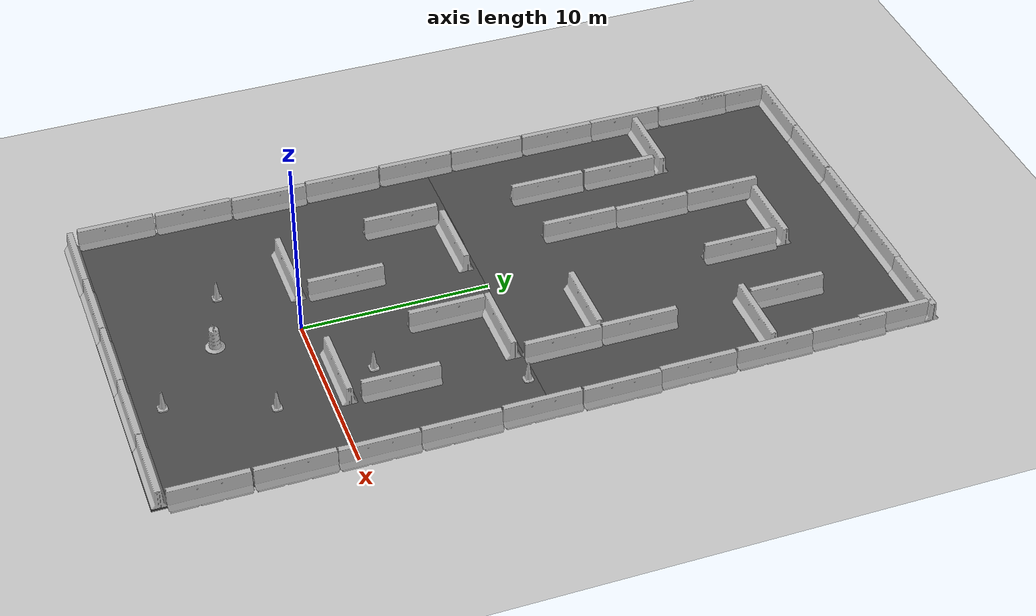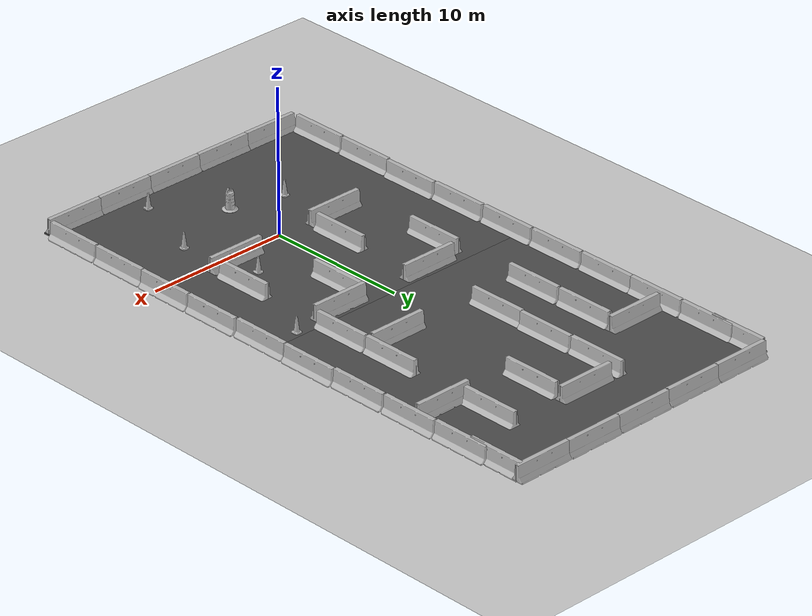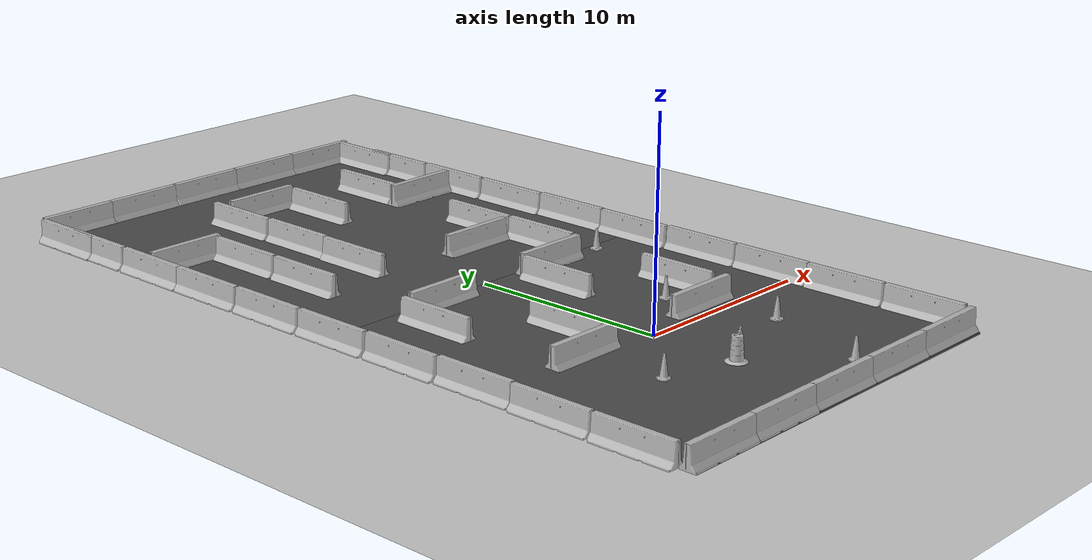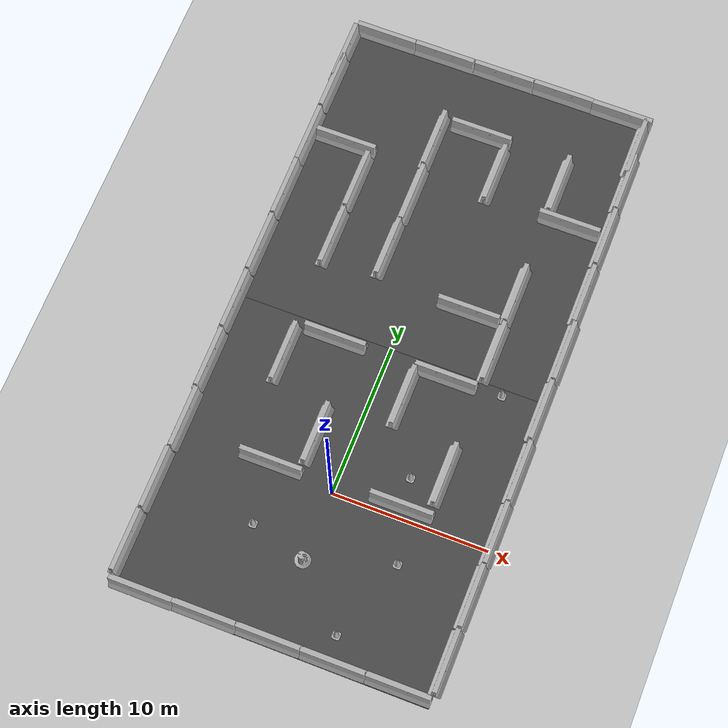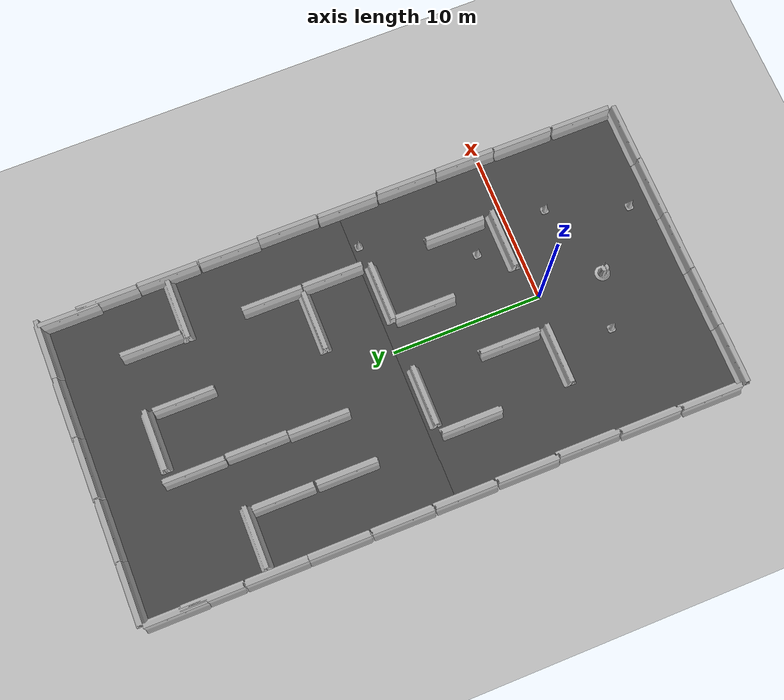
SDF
<sdf version="1.6">
 <world name="default">
  <light name="sun" type="directional">
   <pose>0 0 10 0 -0 0</pose>
   <diffuse>0.8 0.8 0.8 1</diffuse>
   <specular>0.2 0.2 0.2 1</specular>
   <attenuation>
    <range>1000</range>
    <constant>0.9</constant>
    <linear>0.01</linear>
    <quadratic>0.001</quadratic>
   </attenuation>
   <direction>-0.5 0.1 -0.9</direction>
  </light>
  <model name="ground_plane">
   <static>1</static>
   <link name="link">
    <collision name="collision">
     <geometry><plane><normal>0 0 1</normal><size>100 100</size></plane></geometry>
     <surface><friction><ode><mu>100</mu><mu2>50</mu2></ode></friction></surface>
    </collision>
    <visual name="visual">
     <cast_shadows>0</cast_shadows>
     <geometry><plane><normal>0 0 1</normal><size>100 100</size></plane></geometry>
     <material>
      <script><uri>file://media/materials/scripts/gazebo.material</uri><name>Gazebo/Grey</name></script>
     </material>
    </visual>
   </link>
  </model>
  <gravity>0 0 -9.8</gravity>
  <magnetic_field>6e-06 2.3e-05 -4.2e-05</magnetic_field>
  <atmosphere type="adiabatic"/>
  <physics name="default_physics" default="0" type="ode">
   <max_step_size>0.001</max_step_size>
   <real_time_factor>1</real_time_factor>
   <real_time_update_rate>1000</real_time_update_rate>
  </physics>
  <scene><ambient>0.4 0.4 0.4 1</ambient><background>0.7 0.7 0.7 1</background><shadows>1</shadows></scene>
  <spherical_coordinates>
   <surface_model>EARTH_WGS84</surface_model>
   <latitude_deg>0</latitude_deg>
   <longitude_deg>0</longitude_deg>
   <elevation>0</elevation>
   <heading_deg>0</heading_deg>
  </spherical_coordinates>
  <model name="asphalt_plane">
   <static>1</static>
   <link name="link">
    <collision name="collision"><geometry><box><size>20 20 0.1</size></box></geometry></collision>
    <visual name="visual">
     <cast_shadows>0</cast_shadows>
     <geometry><box><size>20 20 0.1</size></box></geometry>
     <material>
      <script>
       <uri>model://asphalt_plane/materials/scripts</uri>
       <uri>model://asphalt_plane/materials/textures</uri>
       <name>vrc/asphalt</name>
      </script>
     </material>
    </visual>
   </link>
   <pose>0.010541 -0.044599 0 0 -0 0</pose>
  </model>
  <model name="asphalt_plane_0">
   <static>1</static>
   <link name="link">
    <collision name="collision"><geometry><box><size>20 20 0.1</size></box></geometry></collision>
    <visual name="visual">
     <cast_shadows>0</cast_shadows>
     <geometry><box><size>20 20 0.1</size></box></geometry>
     <material>
      <script>
       <uri>model://asphalt_plane/materials/scripts</uri>
       <uri>model://asphalt_plane/materials/textures</uri>
       <name>vrc/asphalt</name>
      </script>
     </material>
    </visual>
   </link>
   <pose>-0.000537 19.9198 0 0 -0 0</pose>
  </model>
  <model name="jersey_barrier">
   <static>1</static>
   <link name="link">
    <visual name="visual">
     <geometry><mesh><uri>model://jersey_barrier/meshes/jersey_barrier.dae</uri></mesh></geometry>
    </visual>
    <collision name="upright">
     <pose>0 0 0.5715 0 -0 0</pose>
     <geometry><box><size>4.06542 0.3063 1.143</size></box></geometry>
    </collision>
    <collision name="base">
     <pose>0 0 0.032258 0 -0 0</pose>
     <geometry><box><size>4.06542 0.8107 0.064516</size></box></geometry>
    </collision>
    <collision name="base2">
     <pose>0 0 0.1 0 -0 0</pose>
     <geometry><box><size>4.06542 0.65 0.1</size></box></geometry>
    </collision>
    <collision name="base3">
     <pose>0 0 0.2 0 -0 0</pose>
     <geometry><box><size>4.06542 0.5 0.1</size></box></geometry>
    </collision>
    <collision name="left-angle">
     <pose>0 -0.224 0.2401 0.9 -0 0</pose>
     <geometry><box><size>4.06542 0.5 0.064516</size></box></geometry>
    </collision>
    <collision name="right-angle">
     <pose>0 0.224 0.2401 -0.9 0 0</pose>
     <geometry><box><size>4.06542 0.5 0.064516</size></box></geometry>
    </collision>
   </link>
   <pose>7.99065 -9.61442 0 0 -0 0</pose>
  </model>
  <model name="jersey_barrier_clone">
   <static>1</static>
   <link name="link">
    <visual name="visual">
     <geometry><mesh><uri>model://jersey_barrier/meshes/jersey_barrier.dae</uri></mesh></geometry>
    </visual>
    <collision name="upright">
     <pose>0 0 0.5715 0 -0 0</pose>
     <geometry><box><size>4.06542 0.3063 1.143</size></box></geometry>
    </collision>
    <collision name="base">
     <pose>0 0 0.032258 0 -0 0</pose>
     <geometry><box><size>4.06542 0.8107 0.064516</size></box></geometry>
    </collision>
    <collision name="base2">
     <pose>0 0 0.1 0 -0 0</pose>
     <geometry><box><size>4.06542 0.65 0.1</size></box></geometry>
    </collision>
    <collision name="base3">
     <pose>0 0 0.2 0 -0 0</pose>
     <geometry><box><size>4.06542 0.5 0.1</size></box></geometry>
    </collision>
    <collision name="left-angle">
     <pose>0 -0.224 0.2401 0.9 -0 0</pose>
     <geometry><box><size>4.06542 0.5 0.064516</size></box></geometry>
    </collision>
    <collision name="right-angle">
     <pose>0 0.224 0.2401 -0.9 0 0</pose>
     <geometry><box><size>4.06542 0.5 0.064516</size></box></geometry>
    </collision>
   </link>
   <pose>3.92686 -9.63135 0 0 -0 0</pose>
  </model>
  <model name="jersey_barrier_clone_0">
   <static>1</static>
   <link name="link">
    <visual name="visual">
     <geometry><mesh><uri>model://jersey_barrier/meshes/jersey_barrier.dae</uri></mesh></geometry>
    </visual>
    <collision name="upright">
     <pose>0 0 0.5715 0 -0 0</pose>
     <geometry><box><size>4.06542 0.3063 1.143</size></box></geometry>
    </collision>
    <collision name="base">
     <pose>0 0 0.032258 0 -0 0</pose>
     <geometry><box><size>4.06542 0.8107 0.064516</size></box></geometry>
    </collision>
    <collision name="base2">
     <pose>0 0 0.1 0 -0 0</pose>
     <geometry><box><size>4.06542 0.65 0.1</size></box></geometry>
    </collision>
    <collision name="base3">
     <pose>0 0 0.2 0 -0 0</pose>
     <geometry><box><size>4.06542 0.5 0.1</size></box></geometry>
    </collision>
    <collision name="left-angle">
     <pose>0 -0.224 0.2401 0.9 -0 0</pose>
     <geometry><box><size>4.06542 0.5 0.064516</size></box></geometry>
    </collision>
    <collision name="right-angle">
     <pose>0 0.224 0.2401 -0.9 0 0</pose>
     <geometry><box><size>4.06542 0.5 0.064516</size></box></geometry>
    </collision>
   </link>
   <pose>-0.107331 -9.63265 0 0 -0 0</pose>
  </model>
  <model name="jersey_barrier_clone_1">
   <static>1</static>
   <link name="link">
    <visual name="visual">
     <geometry><mesh><uri>model://jersey_barrier/meshes/jersey_barrier.dae</uri></mesh></geometry>
    </visual>
    <collision name="upright">
     <pose>0 0 0.5715 0 -0 0</pose>
     <geometry><box><size>4.06542 0.3063 1.143</size></box></geometry>
    </collision>
    <collision name="base">
     <pose>0 0 0.032258 0 -0 0</pose>
     <geometry><box><size>4.06542 0.8107 0.064516</size></box></geometry>
    </collision>
    <collision name="base2">
     <pose>0 0 0.1 0 -0 0</pose>
     <geometry><box><size>4.06542 0.65 0.1</size></box></geometry>
    </collision>
    <collision name="base3">
     <pose>0 0 0.2 0 -0 0</pose>
     <geometry><box><size>4.06542 0.5 0.1</size></box></geometry>
    </collision>
    <collision name="left-angle">
     <pose>0 -0.224 0.2401 0.9 -0 0</pose>
     <geometry><box><size>4.06542 0.5 0.064516</size></box></geometry>
    </collision>
    <collision name="right-angle">
     <pose>0 0.224 0.2401 -0.9 0 0</pose>
     <geometry><box><size>4.06542 0.5 0.064516</size></box></geometry>
    </collision>
   </link>
   <pose>-4.16052 -9.65157 0 0 -0 0</pose>
  </model>
  <model name="jersey_barrier_clone_2">
   <static>1</static>
   <link name="link">
    <visual name="visual">
     <geometry><mesh><uri>model://jersey_barrier/meshes/jersey_barrier.dae</uri></mesh></geometry>
    </visual>
    <collision name="upright">
     <pose>0 0 0.5715 0 -0 0</pose>
     <geometry><box><size>4.06542 0.3063 1.143</size></box></geometry>
    </collision>
    <collision name="base">
     <pose>0 0 0.032258 0 -0 0</pose>
     <geometry><box><size>4.06542 0.8107 0.064516</size></box></geometry>
    </collision>
    <collision name="base2">
     <pose>0 0 0.1 0 -0 0</pose>
     <geometry><box><size>4.06542 0.65 0.1</size></box></geometry>
    </collision>
    <collision name="base3">
     <pose>0 0 0.2 0 -0 0</pose>
     <geometry><box><size>4.06542 0.5 0.1</size></box></geometry>
    </collision>
    <collision name="left-angle">
     <pose>0 -0.224 0.2401 0.9 -0 0</pose>
     <geometry><box><size>4.06542 0.5 0.064516</size></box></geometry>
    </collision>
    <collision name="right-angle">
     <pose>0 0.224 0.2401 -0.9 0 0</pose>
     <geometry><box><size>4.06542 0.5 0.064516</size></box></geometry>
    </collision>
   </link>
   <pose>-8.15582 -9.68062 0 0 -0 0</pose>
  </model>
  <model name="jersey_barrier_0">
   <static>1</static>
   <link name="link">
    <visual name="visual">
     <geometry><mesh><uri>model://jersey_barrier/meshes/jersey_barrier.dae</uri></mesh></geometry>
    </visual>
    <collision name="upright">
     <pose>0 0 0.5715 0 -0 0</pose>
     <geometry><box><size>4.06542 0.3063 1.143</size></box></geometry>
    </collision>
    <collision name="base">
     <pose>0 0 0.032258 0 -0 0</pose>
     <geometry><box><size>4.06542 0.8107 0.064516</size></box></geometry>
    </collision>
    <collision name="base2">
     <pose>0 0 0.1 0 -0 0</pose>
     <geometry><box><size>4.06542 0.65 0.1</size></box></geometry>
    </collision>
    <collision name="base3">
     <pose>0 0 0.2 0 -0 0</pose>
     <geometry><box><size>4.06542 0.5 0.1</size></box></geometry>
    </collision>
    <collision name="left-angle">
     <pose>0 -0.224 0.2401 0.9 -0 0</pose>
     <geometry><box><size>4.06542 0.5 0.064516</size></box></geometry>
    </collision>
    <collision name="right-angle">
     <pose>0 0.224 0.2401 -0.9 0 0</pose>
     <geometry><box><size>4.06542 0.5 0.064516</size></box></geometry>
    </collision>
   </link>
   <pose>-10.1903 -7.24742 0 0 -0 1.57</pose>
  </model>
  <model name="jersey_barrier_0_clone">
   <static>1</static>
   <link name="link">
    <visual name="visual">
     <geometry><mesh><uri>model://jersey_barrier/meshes/jersey_barrier.dae</uri></mesh></geometry>
    </visual>
    <collision name="upright">
     <pose>0 0 0.5715 0 -0 0</pose>
     <geometry><box><size>4.06542 0.3063 1.143</size></box></geometry>
    </collision>
    <collision name="base">
     <pose>0 0 0.032258 0 -0 0</pose>
     <geometry><box><size>4.06542 0.8107 0.064516</size></box></geometry>
    </collision>
    <collision name="base2">
     <pose>0 0 0.1 0 -0 0</pose>
     <geometry><box><size>4.06542 0.65 0.1</size></box></geometry>
    </collision>
    <collision name="base3">
     <pose>0 0 0.2 0 -0 0</pose>
     <geometry><box><size>4.06542 0.5 0.1</size></box></geometry>
    </collision>
    <collision name="left-angle">
     <pose>0 -0.224 0.2401 0.9 -0 0</pose>
     <geometry><box><size>4.06542 0.5 0.064516</size></box></geometry>
    </collision>
    <collision name="right-angle">
     <pose>0 0.224 0.2401 -0.9 0 0</pose>
     <geometry><box><size>4.06542 0.5 0.064516</size></box></geometry>
    </collision>
   </link>
   <pose>-10.1525 -3.07801 0 0 -0 1.57</pose>
  </model>
  <model name="jersey_barrier_0_clone_0">
   <static>1</static>
   <link name="link">
    <visual name="visual">
     <geometry><mesh><uri>model://jersey_barrier/meshes/jersey_barrier.dae</uri></mesh></geometry>
    </visual>
    <collision name="upright">
     <pose>0 0 0.5715 0 -0 0</pose>
     <geometry><box><size>4.06542 0.3063 1.143</size></box></geometry>
    </collision>
    <collision name="base">
     <pose>0 0 0.032258 0 -0 0</pose>
     <geometry><box><size>4.06542 0.8107 0.064516</size></box></geometry>
    </collision>
    <collision name="base2">
     <pose>0 0 0.1 0 -0 0</pose>
     <geometry><box><size>4.06542 0.65 0.1</size></box></geometry>
    </collision>
    <collision name="base3">
     <pose>0 0 0.2 0 -0 0</pose>
     <geometry><box><size>4.06542 0.5 0.1</size></box></geometry>
    </collision>
    <collision name="left-angle">
     <pose>0 -0.224 0.2401 0.9 -0 0</pose>
     <geometry><box><size>4.06542 0.5 0.064516</size></box></geometry>
    </collision>
    <collision name="right-angle">
     <pose>0 0.224 0.2401 -0.9 0 0</pose>
     <geometry><box><size>4.06542 0.5 0.064516</size></box></geometry>
    </collision>
   </link>
   <pose>-10.0557 1.05787 0 0 -0 1.57</pose>
  </model>
  <model name="jersey_barrier_0_clone_1">
   <static>1</static>
   <link name="link">
    <visual name="visual">
     <geometry><mesh><uri>model://jersey_barrier/meshes/jersey_barrier.dae</uri></mesh></geometry>
    </visual>
    <collision name="upright">
     <pose>0 0 0.5715 0 -0 0</pose>
     <geometry><box><size>4.06542 0.3063 1.143</size></box></geometry>
    </collision>
    <collision name="base">
     <pose>0 0 0.032258 0 -0 0</pose>
     <geometry><box><size>4.06542 0.8107 0.064516</size></box></geometry>
    </collision>
    <collision name="base2">
     <pose>0 0 0.1 0 -0 0</pose>
     <geometry><box><size>4.06542 0.65 0.1</size></box></geometry>
    </collision>
    <collision name="base3">
     <pose>0 0 0.2 0 -0 0</pose>
     <geometry><box><size>4.06542 0.5 0.1</size></box></geometry>
    </collision>
    <collision name="left-angle">
     <pose>0 -0.224 0.2401 0.9 -0 0</pose>
     <geometry><box><size>4.06542 0.5 0.064516</size></box></geometry>
    </collision>
    <collision name="right-angle">
     <pose>0 0.224 0.2401 -0.9 0 0</pose>
     <geometry><box><size>4.06542 0.5 0.064516</size></box></geometry>
    </collision>
   </link>
   <pose>-10.1433 5.17446 0 0 -0 1.57</pose>
  </model>
  <model name="jersey_barrier_0_clone_2">
   <static>1</static>
   <link name="link">
    <visual name="visual">
     <geometry><mesh><uri>model://jersey_barrier/meshes/jersey_barrier.dae</uri></mesh></geometry>
    </visual>
    <collision name="upright">
     <pose>0 0 0.5715 0 -0 0</pose>
     <geometry><box><size>4.06542 0.3063 1.143</size></box></geometry>
    </collision>
    <collision name="base">
     <pose>0 0 0.032258 0 -0 0</pose>
     <geometry><box><size>4.06542 0.8107 0.064516</size></box></geometry>
    </collision>
    <collision name="base2">
     <pose>0 0 0.1 0 -0 0</pose>
     <geometry><box><size>4.06542 0.65 0.1</size></box></geometry>
    </collision>
    <collision name="base3">
     <pose>0 0 0.2 0 -0 0</pose>
     <geometry><box><size>4.06542 0.5 0.1</size></box></geometry>
    </collision>
    <collision name="left-angle">
     <pose>0 -0.224 0.2401 0.9 -0 0</pose>
     <geometry><box><size>4.06542 0.5 0.064516</size></box></geometry>
    </collision>
    <collision name="right-angle">
     <pose>0 0.224 0.2401 -0.9 0 0</pose>
     <geometry><box><size>4.06542 0.5 0.064516</size></box></geometry>
    </collision>
   </link>
   <pose>-10.1908 9.33826 0 0 -0 1.57</pose>
  </model>
  <model name="jersey_barrier_0_clone_3">
   <static>1</static>
   <link name="link">
    <visual name="visual">
     <geometry><mesh><uri>model://jersey_barrier/meshes/jersey_barrier.dae</uri></mesh></geometry>
    </visual>
    <collision name="upright">
     <pose>0 0 0.5715 0 -0 0</pose>
     <geometry><box><size>4.06542 0.3063 1.143</size></box></geometry>
    </collision>
    <collision name="base">
     <pose>0 0 0.032258 0 -0 0</pose>
     <geometry><box><size>4.06542 0.8107 0.064516</size></box></geometry>
    </collision>
    <collision name="base2">
     <pose>0 0 0.1 0 -0 0</pose>
     <geometry><box><size>4.06542 0.65 0.1</size></box></geometry>
    </collision>
    <collision name="base3">
     <pose>0 0 0.2 0 -0 0</pose>
     <geometry><box><size>4.06542 0.5 0.1</size></box></geometry>
    </collision>
    <collision name="left-angle">
     <pose>0 -0.224 0.2401 0.9 -0 0</pose>
     <geometry><box><size>4.06542 0.5 0.064516</size></box></geometry>
    </collision>
    <collision name="right-angle">
     <pose>0 0.224 0.2401 -0.9 0 0</pose>
     <geometry><box><size>4.06542 0.5 0.064516</size></box></geometry>
    </collision>
   </link>
   <pose>-10.2097 13.4787 0 0 -0 1.57</pose>
  </model>
  <model name="jersey_barrier_0_clone_4">
   <static>1</static>
   <link name="link">
    <visual name="visual">
     <geometry><mesh><uri>model://jersey_barrier/meshes/jersey_barrier.dae</uri></mesh></geometry>
    </visual>
    <collision name="upright">
     <pose>0 0 0.5715 0 -0 0</pose>
     <geometry><box><size>4.06542 0.3063 1.143</size></box></geometry>
    </collision>
    <collision name="base">
     <pose>0 0 0.032258 0 -0 0</pose>
     <geometry><box><size>4.06542 0.8107 0.064516</size></box></geometry>
    </collision>
    <collision name="base2">
     <pose>0 0 0.1 0 -0 0</pose>
     <geometry><box><size>4.06542 0.65 0.1</size></box></geometry>
    </collision>
    <collision name="base3">
     <pose>0 0 0.2 0 -0 0</pose>
     <geometry><box><size>4.06542 0.5 0.1</size></box></geometry>
    </collision>
    <collision name="left-angle">
     <pose>0 -0.224 0.2401 0.9 -0 0</pose>
     <geometry><box><size>4.06542 0.5 0.064516</size></box></geometry>
    </collision>
    <collision name="right-angle">
     <pose>0 0.224 0.2401 -0.9 0 0</pose>
     <geometry><box><size>4.06542 0.5 0.064516</size></box></geometry>
    </collision>
   </link>
   <pose>-10.2285 17.6199 0 0 -0 1.57</pose>
  </model>
  <model name="jersey_barrier_0_clone_5">
   <static>1</static>
   <link name="link">
    <visual name="visual">
     <geometry><mesh><uri>model://jersey_barrier/meshes/jersey_barrier.dae</uri></mesh></geometry>
    </visual>
    <collision name="upright">
     <pose>0 0 0.5715 0 -0 0</pose>
     <geometry><box><size>4.06542 0.3063 1.143</size></box></geometry>
    </collision>
    <collision name="base">
     <pose>0 0 0.032258 0 -0 0</pose>
     <geometry><box><size>4.06542 0.8107 0.064516</size></box></geometry>
    </collision>
    <collision name="base2">
     <pose>0 0 0.1 0 -0 0</pose>
     <geometry><box><size>4.06542 0.65 0.1</size></box></geometry>
    </collision>
    <collision name="base3">
     <pose>0 0 0.2 0 -0 0</pose>
     <geometry><box><size>4.06542 0.5 0.1</size></box></geometry>
    </collision>
    <collision name="left-angle">
     <pose>0 -0.224 0.2401 0.9 -0 0</pose>
     <geometry><box><size>4.06542 0.5 0.064516</size></box></geometry>
    </collision>
    <collision name="right-angle">
     <pose>0 0.224 0.2401 -0.9 0 0</pose>
     <geometry><box><size>4.06542 0.5 0.064516</size></box></geometry>
    </collision>
   </link>
   <pose>-10.2364 21.6611 0 0 -0 1.57</pose>
  </model>
  <model name="jersey_barrier_0_clone_6">
   <static>1</static>
   <link name="link">
    <visual name="visual">
     <geometry><mesh><uri>model://jersey_barrier/meshes/jersey_barrier.dae</uri></mesh></geometry>
    </visual>
    <collision name="upright">
     <pose>0 0 0.5715 0 -0 0</pose>
     <geometry><box><size>4.06542 0.3063 1.143</size></box></geometry>
    </collision>
    <collision name="base">
     <pose>0 0 0.032258 0 -0 0</pose>
     <geometry><box><size>4.06542 0.8107 0.064516</size></box></geometry>
    </collision>
    <collision name="base2">
     <pose>0 0 0.1 0 -0 0</pose>
     <geometry><box><size>4.06542 0.65 0.1</size></box></geometry>
    </collision>
    <collision name="base3">
     <pose>0 0 0.2 0 -0 0</pose>
     <geometry><box><size>4.06542 0.5 0.1</size></box></geometry>
    </collision>
    <collision name="left-angle">
     <pose>0 -0.224 0.2401 0.9 -0 0</pose>
     <geometry><box><size>4.06542 0.5 0.064516</size></box></geometry>
    </collision>
    <collision name="right-angle">
     <pose>0 0.224 0.2401 -0.9 0 0</pose>
     <geometry><box><size>4.06542 0.5 0.064516</size></box></geometry>
    </collision>
   </link>
   <pose>-10.2327 25.7998 0 0 -0 1.57</pose>
  </model>
  <model name="jersey_barrier_0_clone_7">
   <static>1</static>
   <link name="link">
    <visual name="visual">
     <geometry><mesh><uri>model://jersey_barrier/meshes/jersey_barrier.dae</uri></mesh></geometry>
    </visual>
    <collision name="upright">
     <pose>0 0 0.5715 0 -0 0</pose>
     <geometry><box><size>4.06542 0.3063 1.143</size></box></geometry>
    </collision>
    <collision name="base">
     <pose>0 0 0.032258 0 -0 0</pose>
     <geometry><box><size>4.06542 0.8107 0.064516</size></box></geometry>
    </collision>
    <collision name="base2">
     <pose>0 0 0.1 0 -0 0</pose>
     <geometry><box><size>4.06542 0.65 0.1</size></box></geometry>
    </collision>
    <collision name="base3">
     <pose>0 0 0.2 0 -0 0</pose>
     <geometry><box><size>4.06542 0.5 0.1</size></box></geometry>
    </collision>
    <collision name="left-angle">
     <pose>0 -0.224 0.2401 0.9 -0 0</pose>
     <geometry><box><size>4.06542 0.5 0.064516</size></box></geometry>
    </collision>
    <collision name="right-angle">
     <pose>0 0.224 0.2401 -0.9 0 0</pose>
     <geometry><box><size>4.06542 0.5 0.064516</size></box></geometry>
    </collision>
   </link>
   <pose>-10.2894 28.1368 0 0 -0 1.57</pose>
  </model>
  <model name="jersey_barrier_0_clone_8">
   <static>1</static>
   <link name="link">
    <visual name="visual">
     <geometry><mesh><uri>model://jersey_barrier/meshes/jersey_barrier.dae</uri></mesh></geometry>
    </visual>
    <collision name="upright">
     <pose>0 0 0.5715 0 -0 0</pose>
     <geometry><box><size>4.06542 0.3063 1.143</size></box></geometry>
    </collision>
    <collision name="base">
     <pose>0 0 0.032258 0 -0 0</pose>
     <geometry><box><size>4.06542 0.8107 0.064516</size></box></geometry>
    </collision>
    <collision name="base2">
     <pose>0 0 0.1 0 -0 0</pose>
     <geometry><box><size>4.06542 0.65 0.1</size></box></geometry>
    </collision>
    <collision name="base3">
     <pose>0 0 0.2 0 -0 0</pose>
     <geometry><box><size>4.06542 0.5 0.1</size></box></geometry>
    </collision>
    <collision name="left-angle">
     <pose>0 -0.224 0.2401 0.9 -0 0</pose>
     <geometry><box><size>4.06542 0.5 0.064516</size></box></geometry>
    </collision>
    <collision name="right-angle">
     <pose>0 0.224 0.2401 -0.9 0 0</pose>
     <geometry><box><size>4.06542 0.5 0.064516</size></box></geometry>
    </collision>
   </link>
   <pose>10.0338 -7.23924 0 0 -0 1.57</pose>
  </model>
  <model name="jersey_barrier_0_clone_9">
   <static>1</static>
   <link name="link">
    <visual name="visual">
     <geometry><mesh><uri>model://jersey_barrier/meshes/jersey_barrier.dae</uri></mesh></geometry>
    </visual>
    <collision name="upright">
     <pose>0 0 0.5715 0 -0 0</pose>
     <geometry><box><size>4.06542 0.3063 1.143</size></box></geometry>
    </collision>
    <collision name="base">
     <pose>0 0 0.032258 0 -0 0</pose>
     <geometry><box><size>4.06542 0.8107 0.064516</size></box></geometry>
    </collision>
    <collision name="base2">
     <pose>0 0 0.1 0 -0 0</pose>
     <geometry><box><size>4.06542 0.65 0.1</size></box></geometry>
    </collision>
    <collision name="base3">
     <pose>0 0 0.2 0 -0 0</pose>
     <geometry><box><size>4.06542 0.5 0.1</size></box></geometry>
    </collision>
    <collision name="left-angle">
     <pose>0 -0.224 0.2401 0.9 -0 0</pose>
     <geometry><box><size>4.06542 0.5 0.064516</size></box></geometry>
    </collision>
    <collision name="right-angle">
     <pose>0 0.224 0.2401 -0.9 0 0</pose>
     <geometry><box><size>4.06542 0.5 0.064516</size></box></geometry>
    </collision>
   </link>
   <pose>10.0508 -3.08382 0 0 -0 1.57</pose>
  </model>
  <model name="jersey_barrier_0_clone_10">
   <static>1</static>
   <link name="link">
    <visual name="visual">
     <geometry><mesh><uri>model://jersey_barrier/meshes/jersey_barrier.dae</uri></mesh></geometry>
    </visual>
    <collision name="upright">
     <pose>0 0 0.5715 0 -0 0</pose>
     <geometry><box><size>4.06542 0.3063 1.143</size></box></geometry>
    </collision>
    <collision name="base">
     <pose>0 0 0.032258 0 -0 0</pose>
     <geometry><box><size>4.06542 0.8107 0.064516</size></box></geometry>
    </collision>
    <collision name="base2">
     <pose>0 0 0.1 0 -0 0</pose>
     <geometry><box><size>4.06542 0.65 0.1</size></box></geometry>
    </collision>
    <collision name="base3">
     <pose>0 0 0.2 0 -0 0</pose>
     <geometry><box><size>4.06542 0.5 0.1</size></box></geometry>
    </collision>
    <collision name="left-angle">
     <pose>0 -0.224 0.2401 0.9 -0 0</pose>
     <geometry><box><size>4.06542 0.5 0.064516</size></box></geometry>
    </collision>
    <collision name="right-angle">
     <pose>0 0.224 0.2401 -0.9 0 0</pose>
     <geometry><box><size>4.06542 0.5 0.064516</size></box></geometry>
    </collision>
   </link>
   <pose>10.091 1.01244 0 0 -0 1.57</pose>
  </model>
  <model name="jersey_barrier_0_clone_11">
   <static>1</static>
   <link name="link">
    <visual name="visual">
     <geometry><mesh><uri>model://jersey_barrier/meshes/jersey_barrier.dae</uri></mesh></geometry>
    </visual>
    <collision name="upright">
     <pose>0 0 0.5715 0 -0 0</pose>
     <geometry><box><size>4.06542 0.3063 1.143</size></box></geometry>
    </collision>
    <collision name="base">
     <pose>0 0 0.032258 0 -0 0</pose>
     <geometry><box><size>4.06542 0.8107 0.064516</size></box></geometry>
    </collision>
    <collision name="base2">
     <pose>0 0 0.1 0 -0 0</pose>
     <geometry><box><size>4.06542 0.65 0.1</size></box></geometry>
    </collision>
    <collision name="base3">
     <pose>0 0 0.2 0 -0 0</pose>
     <geometry><box><size>4.06542 0.5 0.1</size></box></geometry>
    </collision>
    <collision name="left-angle">
     <pose>0 -0.224 0.2401 0.9 -0 0</pose>
     <geometry><box><size>4.06542 0.5 0.064516</size></box></geometry>
    </collision>
    <collision name="right-angle">
     <pose>0 0.224 0.2401 -0.9 0 0</pose>
     <geometry><box><size>4.06542 0.5 0.064516</size></box></geometry>
    </collision>
   </link>
   <pose>10.0774 5.12431 0 0 -0 1.57</pose>
  </model>
  <model name="jersey_barrier_0_clone_12">
   <static>1</static>
   <link name="link">
    <visual name="visual">
     <geometry><mesh><uri>model://jersey_barrier/meshes/jersey_barrier.dae</uri></mesh></geometry>
    </visual>
    <collision name="upright">
     <pose>0 0 0.5715 0 -0 0</pose>
     <geometry><box><size>4.06542 0.3063 1.143</size></box></geometry>
    </collision>
    <collision name="base">
     <pose>0 0 0.032258 0 -0 0</pose>
     <geometry><box><size>4.06542 0.8107 0.064516</size></box></geometry>
    </collision>
    <collision name="base2">
     <pose>0 0 0.1 0 -0 0</pose>
     <geometry><box><size>4.06542 0.65 0.1</size></box></geometry>
    </collision>
    <collision name="base3">
     <pose>0 0 0.2 0 -0 0</pose>
     <geometry><box><size>4.06542 0.5 0.1</size></box></geometry>
    </collision>
    <collision name="left-angle">
     <pose>0 -0.224 0.2401 0.9 -0 0</pose>
     <geometry><box><size>4.06542 0.5 0.064516</size></box></geometry>
    </collision>
    <collision name="right-angle">
     <pose>0 0.224 0.2401 -0.9 0 0</pose>
     <geometry><box><size>4.06542 0.5 0.064516</size></box></geometry>
    </collision>
   </link>
   <pose>9.99 9.26218 0 0 -0 1.57</pose>
  </model>
  <model name="jersey_barrier_0_clone_13">
   <static>1</static>
   <link name="link">
    <visual name="visual">
     <geometry><mesh><uri>model://jersey_barrier/meshes/jersey_barrier.dae</uri></mesh></geometry>
    </visual>
    <collision name="upright">
     <pose>0 0 0.5715 0 -0 0</pose>
     <geometry><box><size>4.06542 0.3063 1.143</size></box></geometry>
    </collision>
    <collision name="base">
     <pose>0 0 0.032258 0 -0 0</pose>
     <geometry><box><size>4.06542 0.8107 0.064516</size></box></geometry>
    </collision>
    <collision name="base2">
     <pose>0 0 0.1 0 -0 0</pose>
     <geometry><box><size>4.06542 0.65 0.1</size></box></geometry>
    </collision>
    <collision name="base3">
     <pose>0 0 0.2 0 -0 0</pose>
     <geometry><box><size>4.06542 0.5 0.1</size></box></geometry>
    </collision>
    <collision name="left-angle">
     <pose>0 -0.224 0.2401 0.9 -0 0</pose>
     <geometry><box><size>4.06542 0.5 0.064516</size></box></geometry>
    </collision>
    <collision name="right-angle">
     <pose>0 0.224 0.2401 -0.9 0 0</pose>
     <geometry><box><size>4.06542 0.5 0.064516</size></box></geometry>
    </collision>
   </link>
   <pose>10.0379 13.3795 0 0 -0 1.57</pose>
  </model>
  <model name="jersey_barrier_0_clone_14">
   <static>1</static>
   <link name="link">
    <visual name="visual">
     <geometry><mesh><uri>model://jersey_barrier/meshes/jersey_barrier.dae</uri></mesh></geometry>
    </visual>
    <collision name="upright">
     <pose>0 0 0.5715 0 -0 0</pose>
     <geometry><box><size>4.06542 0.3063 1.143</size></box></geometry>
    </collision>
    <collision name="base">
     <pose>0 0 0.032258 0 -0 0</pose>
     <geometry><box><size>4.06542 0.8107 0.064516</size></box></geometry>
    </collision>
    <collision name="base2">
     <pose>0 0 0.1 0 -0 0</pose>
     <geometry><box><size>4.06542 0.65 0.1</size></box></geometry>
    </collision>
    <collision name="base3">
     <pose>0 0 0.2 0 -0 0</pose>
     <geometry><box><size>4.06542 0.5 0.1</size></box></geometry>
    </collision>
    <collision name="left-angle">
     <pose>0 -0.224 0.2401 0.9 -0 0</pose>
     <geometry><box><size>4.06542 0.5 0.064516</size></box></geometry>
    </collision>
    <collision name="right-angle">
     <pose>0 0.224 0.2401 -0.9 0 0</pose>
     <geometry><box><size>4.06542 0.5 0.064516</size></box></geometry>
    </collision>
   </link>
   <pose>9.92788 17.433 0 0 -0 1.57</pose>
  </model>
  <model name="jersey_barrier_0_clone_15">
   <static>1</static>
   <link name="link">
    <visual name="visual">
     <geometry><mesh><uri>model://jersey_barrier/meshes/jersey_barrier.dae</uri></mesh></geometry>
    </visual>
    <collision name="upright">
     <pose>0 0 0.5715 0 -0 0</pose>
     <geometry><box><size>4.06542 0.3063 1.143</size></box></geometry>
    </collision>
    <collision name="base">
     <pose>0 0 0.032258 0 -0 0</pose>
     <geometry><box><size>4.06542 0.8107 0.064516</size></box></geometry>
    </collision>
    <collision name="base2">
     <pose>0 0 0.1 0 -0 0</pose>
     <geometry><box><size>4.06542 0.65 0.1</size></box></geometry>
    </collision>
    <collision name="base3">
     <pose>0 0 0.2 0 -0 0</pose>
     <geometry><box><size>4.06542 0.5 0.1</size></box></geometry>
    </collision>
    <collision name="left-angle">
     <pose>0 -0.224 0.2401 0.9 -0 0</pose>
     <geometry><box><size>4.06542 0.5 0.064516</size></box></geometry>
    </collision>
    <collision name="right-angle">
     <pose>0 0.224 0.2401 -0.9 0 0</pose>
     <geometry><box><size>4.06542 0.5 0.064516</size></box></geometry>
    </collision>
   </link>
   <pose>9.90367 21.578 0 0 -0 1.57</pose>
  </model>
  <model name="jersey_barrier_0_clone_16">
   <static>1</static>
   <link name="link">
    <visual name="visual">
     <geometry><mesh><uri>model://jersey_barrier/meshes/jersey_barrier.dae</uri></mesh></geometry>
    </visual>
    <collision name="upright">
     <pose>0 0 0.5715 0 -0 0</pose>
     <geometry><box><size>4.06542 0.3063 1.143</size></box></geometry>
    </collision>
    <collision name="base">
     <pose>0 0 0.032258 0 -0 0</pose>
     <geometry><box><size>4.06542 0.8107 0.064516</size></box></geometry>
    </collision>
    <collision name="base2">
     <pose>0 0 0.1 0 -0 0</pose>
     <geometry><box><size>4.06542 0.65 0.1</size></box></geometry>
    </collision>
    <collision name="base3">
     <pose>0 0 0.2 0 -0 0</pose>
     <geometry><box><size>4.06542 0.5 0.1</size></box></geometry>
    </collision>
    <collision name="left-angle">
     <pose>0 -0.224 0.2401 0.9 -0 0</pose>
     <geometry><box><size>4.06542 0.5 0.064516</size></box></geometry>
    </collision>
    <collision name="right-angle">
     <pose>0 0.224 0.2401 -0.9 0 0</pose>
     <geometry><box><size>4.06542 0.5 0.064516</size></box></geometry>
    </collision>
   </link>
   <pose>9.83696 25.6628 0 0 -0 1.57</pose>
  </model>
  <model name="jersey_barrier_0_clone_17">
   <static>1</static>
   <link name="link">
    <visual name="visual">
     <geometry><mesh><uri>model://jersey_barrier/meshes/jersey_barrier.dae</uri></mesh></geometry>
    </visual>
    <collision name="upright">
     <pose>0 0 0.5715 0 -0 0</pose>
     <geometry><box><size>4.06542 0.3063 1.143</size></box></geometry>
    </collision>
    <collision name="base">
     <pose>0 0 0.032258 0 -0 0</pose>
     <geometry><box><size>4.06542 0.8107 0.064516</size></box></geometry>
    </collision>
    <collision name="base2">
     <pose>0 0 0.1 0 -0 0</pose>
     <geometry><box><size>4.06542 0.65 0.1</size></box></geometry>
    </collision>
    <collision name="base3">
     <pose>0 0 0.2 0 -0 0</pose>
     <geometry><box><size>4.06542 0.5 0.1</size></box></geometry>
    </collision>
    <collision name="left-angle">
     <pose>0 -0.224 0.2401 0.9 -0 0</pose>
     <geometry><box><size>4.06542 0.5 0.064516</size></box></geometry>
    </collision>
    <collision name="right-angle">
     <pose>0 0.224 0.2401 -0.9 0 0</pose>
     <geometry><box><size>4.06542 0.5 0.064516</size></box></geometry>
    </collision>
   </link>
   <pose>9.68937 28.3062 0 0 -0 1.57</pose>
  </model>
  <model name="jersey_barrier_1">
   <static>1</static>
   <link name="link">
    <visual name="visual">
     <geometry><mesh><uri>model://jersey_barrier/meshes/jersey_barrier.dae</uri></mesh></geometry>
    </visual>
    <collision name="upright">
     <pose>0 0 0.5715 0 -0 0</pose>
     <geometry><box><size>4.06542 0.3063 1.143</size></box></geometry>
    </collision>
    <collision name="base">
     <pose>0 0 0.032258 0 -0 0</pose>
     <geometry><box><size>4.06542 0.8107 0.064516</size></box></geometry>
    </collision>
    <collision name="base2">
     <pose>0 0 0.1 0 -0 0</pose>
     <geometry><box><size>4.06542 0.65 0.1</size></box></geometry>
    </collision>
    <collision name="base3">
     <pose>0 0 0.2 0 -0 0</pose>
     <geometry><box><size>4.06542 0.5 0.1</size></box></geometry>
    </collision>
    <collision name="left-angle">
     <pose>0 -0.224 0.2401 0.9 -0 0</pose>
     <geometry><box><size>4.06542 0.5 0.064516</size></box></geometry>
    </collision>
    <collision name="right-angle">
     <pose>0 0.224 0.2401 -0.9 0 0</pose>
     <geometry><box><size>4.06542 0.5 0.064516</size></box></geometry>
    </collision>
   </link>
   <pose>-8.16833 30.2907 0 0 -0 0</pose>
  </model>
  <model name="jersey_barrier_1_clone">
   <static>1</static>
   <link name="link">
    <visual name="visual">
     <geometry><mesh><uri>model://jersey_barrier/meshes/jersey_barrier.dae</uri></mesh></geometry>
    </visual>
    <collision name="upright">
     <pose>0 0 0.5715 0 -0 0</pose>
     <geometry><box><size>4.06542 0.3063 1.143</size></box></geometry>
    </collision>
    <collision name="base">
     <pose>0 0 0.032258 0 -0 0</pose>
     <geometry><box><size>4.06542 0.8107 0.064516</size></box></geometry>
    </collision>
    <collision name="base2">
     <pose>0 0 0.1 0 -0 0</pose>
     <geometry><box><size>4.06542 0.65 0.1</size></box></geometry>
    </collision>
    <collision name="base3">
     <pose>0 0 0.2 0 -0 0</pose>
     <geometry><box><size>4.06542 0.5 0.1</size></box></geometry>
    </collision>
    <collision name="left-angle">
     <pose>0 -0.224 0.2401 0.9 -0 0</pose>
     <geometry><box><size>4.06542 0.5 0.064516</size></box></geometry>
    </collision>
    <collision name="right-angle">
     <pose>0 0.224 0.2401 -0.9 0 0</pose>
     <geometry><box><size>4.06542 0.5 0.064516</size></box></geometry>
    </collision>
   </link>
   <pose>-4.11228 30.3005 0 0 -0 0</pose>
  </model>
  <model name="jersey_barrier_1_clone_0">
   <static>1</static>
   <link name="link">
    <visual name="visual">
     <geometry><mesh><uri>model://jersey_barrier/meshes/jersey_barrier.dae</uri></mesh></geometry>
    </visual>
    <collision name="upright">
     <pose>0 0 0.5715 0 -0 0</pose>
     <geometry><box><size>4.06542 0.3063 1.143</size></box></geometry>
    </collision>
    <collision name="base">
     <pose>0 0 0.032258 0 -0 0</pose>
     <geometry><box><size>4.06542 0.8107 0.064516</size></box></geometry>
    </collision>
    <collision name="base2">
     <pose>0 0 0.1 0 -0 0</pose>
     <geometry><box><size>4.06542 0.65 0.1</size></box></geometry>
    </collision>
    <collision name="base3">
     <pose>0 0 0.2 0 -0 0</pose>
     <geometry><box><size>4.06542 0.5 0.1</size></box></geometry>
    </collision>
    <collision name="left-angle">
     <pose>0 -0.224 0.2401 0.9 -0 0</pose>
     <geometry><box><size>4.06542 0.5 0.064516</size></box></geometry>
    </collision>
    <collision name="right-angle">
     <pose>0 0.224 0.2401 -0.9 0 0</pose>
     <geometry><box><size>4.06542 0.5 0.064516</size></box></geometry>
    </collision>
   </link>
   <pose>-5.5e-05 30.3194 0 0 -0 0</pose>
  </model>
  <model name="jersey_barrier_1_clone_1">
   <static>1</static>
   <link name="link">
    <visual name="visual">
     <geometry><mesh><uri>model://jersey_barrier/meshes/jersey_barrier.dae</uri></mesh></geometry>
    </visual>
    <collision name="upright">
     <pose>0 0 0.5715 0 -0 0</pose>
     <geometry><box><size>4.06542 0.3063 1.143</size></box></geometry>
    </collision>
    <collision name="base">
     <pose>0 0 0.032258 0 -0 0</pose>
     <geometry><box><size>4.06542 0.8107 0.064516</size></box></geometry>
    </collision>
    <collision name="base2">
     <pose>0 0 0.1 0 -0 0</pose>
     <geometry><box><size>4.06542 0.65 0.1</size></box></geometry>
    </collision>
    <collision name="base3">
     <pose>0 0 0.2 0 -0 0</pose>
     <geometry><box><size>4.06542 0.5 0.1</size></box></geometry>
    </collision>
    <collision name="left-angle">
     <pose>0 -0.224 0.2401 0.9 -0 0</pose>
     <geometry><box><size>4.06542 0.5 0.064516</size></box></geometry>
    </collision>
    <collision name="right-angle">
     <pose>0 0.224 0.2401 -0.9 0 0</pose>
     <geometry><box><size>4.06542 0.5 0.064516</size></box></geometry>
    </collision>
   </link>
   <pose>4.06912 30.3372 0 0 -0 0</pose>
  </model>
  <model name="jersey_barrier_1_clone_2">
   <static>1</static>
   <link name="link">
    <visual name="visual">
     <geometry><mesh><uri>model://jersey_barrier/meshes/jersey_barrier.dae</uri></mesh></geometry>
    </visual>
    <collision name="upright">
     <pose>0 0 0.5715 0 -0 0</pose>
     <geometry><box><size>4.06542 0.3063 1.143</size></box></geometry>
    </collision>
    <collision name="base">
     <pose>0 0 0.032258 0 -0 0</pose>
     <geometry><box><size>4.06542 0.8107 0.064516</size></box></geometry>
    </collision>
    <collision name="base2">
     <pose>0 0 0.1 0 -0 0</pose>
     <geometry><box><size>4.06542 0.65 0.1</size></box></geometry>
    </collision>
    <collision name="base3">
     <pose>0 0 0.2 0 -0 0</pose>
     <geometry><box><size>4.06542 0.5 0.1</size></box></geometry>
    </collision>
    <collision name="left-angle">
     <pose>0 -0.224 0.2401 0.9 -0 0</pose>
     <geometry><box><size>4.06542 0.5 0.064516</size></box></geometry>
    </collision>
    <collision name="right-angle">
     <pose>0 0.224 0.2401 -0.9 0 0</pose>
     <geometry><box><size>4.06542 0.5 0.064516</size></box></geometry>
    </collision>
   </link>
   <pose>8.07985 30.301 0 0 -0 0</pose>
  </model>
  <model name="jersey_barrier_1_clone_3">
   <static>1</static>
   <link name="link">
    <visual name="visual">
     <geometry><mesh><uri>model://jersey_barrier/meshes/jersey_barrier.dae</uri></mesh></geometry>
    </visual>
    <collision name="upright">
     <pose>0 0 0.5715 0 -0 0</pose>
     <geometry><box><size>4.06542 0.3063 1.143</size></box></geometry>
    </collision>
    <collision name="base">
     <pose>0 0 0.032258 0 -0 0</pose>
     <geometry><box><size>4.06542 0.8107 0.064516</size></box></geometry>
    </collision>
    <collision name="base2">
     <pose>0 0 0.1 0 -0 0</pose>
     <geometry><box><size>4.06542 0.65 0.1</size></box></geometry>
    </collision>
    <collision name="base3">
     <pose>0 0 0.2 0 -0 0</pose>
     <geometry><box><size>4.06542 0.5 0.1</size></box></geometry>
    </collision>
    <collision name="left-angle">
     <pose>0 -0.224 0.2401 0.9 -0 0</pose>
     <geometry><box><size>4.06542 0.5 0.064516</size></box></geometry>
    </collision>
    <collision name="right-angle">
     <pose>0 0.224 0.2401 -0.9 0 0</pose>
     <geometry><box><size>4.06542 0.5 0.064516</size></box></geometry>
    </collision>
   </link>
   <pose>-4.09475 0.466008 0 0 -0 0</pose>
  </model>
  <model name="jersey_barrier_1_clone_4">
   <static>1</static>
   <link name="link">
    <visual name="visual">
     <geometry><mesh><uri>model://jersey_barrier/meshes/jersey_barrier.dae</uri></mesh></geometry>
    </visual>
    <collision name="upright">
     <pose>0 0 0.5715 0 -0 0</pose>
     <geometry><box><size>4.06542 0.3063 1.143</size></box></geometry>
    </collision>
    <collision name="base">
     <pose>0 0 0.032258 0 -0 0</pose>
     <geometry><box><size>4.06542 0.8107 0.064516</size></box></geometry>
    </collision>
    <collision name="base2">
     <pose>0 0 0.1 0 -0 0</pose>
     <geometry><box><size>4.06542 0.65 0.1</size></box></geometry>
    </collision>
    <collision name="base3">
     <pose>0 0 0.2 0 -0 0</pose>
     <geometry><box><size>4.06542 0.5 0.1</size></box></geometry>
    </collision>
    <collision name="left-angle">
     <pose>0 -0.224 0.2401 0.9 -0 0</pose>
     <geometry><box><size>4.06542 0.5 0.064516</size></box></geometry>
    </collision>
    <collision name="right-angle">
     <pose>0 0.224 0.2401 -0.9 0 0</pose>
     <geometry><box><size>4.06542 0.5 0.064516</size></box></geometry>
    </collision>
   </link>
   <pose>4.22511 0.708819 0 0 -0 0</pose>
  </model>
  <model name="jersey_barrier_0_clone_11_clone">
   <static>1</static>
   <link name="link">
    <visual name="visual">
     <geometry><mesh><uri>model://jersey_barrier/meshes/jersey_barrier.dae</uri></mesh></geometry>
    </visual>
    <collision name="upright">
     <pose>0 0 0.5715 0 -0 0</pose>
     <geometry><box><size>4.06542 0.3063 1.143</size></box></geometry>
    </collision>
    <collision name="base">
     <pose>0 0 0.032258 0 -0 0</pose>
     <geometry><box><size>4.06542 0.8107 0.064516</size></box></geometry>
    </collision>
    <collision name="base2">
     <pose>0 0 0.1 0 -0 0</pose>
     <geometry><box><size>4.06542 0.65 0.1</size></box></geometry>
    </collision>
    <collision name="base3">
     <pose>0 0 0.2 0 -0 0</pose>
     <geometry><box><size>4.06542 0.5 0.1</size></box></geometry>
    </collision>
    <collision name="left-angle">
     <pose>0 -0.224 0.2401 0.9 -0 0</pose>
     <geometry><box><size>4.06542 0.5 0.064516</size></box></geometry>
    </collision>
    <collision name="right-angle">
     <pose>0 0.224 0.2401 -0.9 0 0</pose>
     <geometry><box><size>4.06542 0.5 0.064516</size></box></geometry>
    </collision>
   </link>
   <pose>5.96451 3.38886 0 0 -0 1.57</pose>
  </model>
  <model name="jersey_barrier_0_clone_11_clone_1">
   <static>1</static>
   <link name="link">
    <visual name="visual">
     <geometry><mesh><uri>model://jersey_barrier/meshes/jersey_barrier.dae</uri></mesh></geometry>
    </visual>
    <collision name="upright">
     <pose>0 0 0.5715 0 -0 0</pose>
     <geometry><box><size>4.06542 0.3063 1.143</size></box></geometry>
    </collision>
    <collision name="base">
     <pose>0 0 0.032258 0 -0 0</pose>
     <geometry><box><size>4.06542 0.8107 0.064516</size></box></geometry>
    </collision>
    <collision name="base2">
     <pose>0 0 0.1 0 -0 0</pose>
     <geometry><box><size>4.06542 0.65 0.1</size></box></geometry>
    </collision>
    <collision name="base3">
     <pose>0 0 0.2 0 -0 0</pose>
     <geometry><box><size>4.06542 0.5 0.1</size></box></geometry>
    </collision>
    <collision name="left-angle">
     <pose>0 -0.224 0.2401 0.9 -0 0</pose>
     <geometry><box><size>4.06542 0.5 0.064516</size></box></geometry>
    </collision>
    <collision name="right-angle">
     <pose>0 0.224 0.2401 -0.9 0 0</pose>
     <geometry><box><size>4.06542 0.5 0.064516</size></box></geometry>
    </collision>
   </link>
   <pose>5.98804 11.8358 0 0 -0 1.57</pose>
  </model>
  <model name="jersey_barrier_0_clone_11_clone_2">
   <static>1</static>
   <link name="link">
    <visual name="visual">
     <geometry><mesh><uri>model://jersey_barrier/meshes/jersey_barrier.dae</uri></mesh></geometry>
    </visual>
    <collision name="upright">
     <pose>0 0 0.5715 0 -0 0</pose>
     <geometry><box><size>4.06542 0.3063 1.143</size></box></geometry>
    </collision>
    <collision name="base">
     <pose>0 0 0.032258 0 -0 0</pose>
     <geometry><box><size>4.06542 0.8107 0.064516</size></box></geometry>
    </collision>
    <collision name="base2">
     <pose>0 0 0.1 0 -0 0</pose>
     <geometry><box><size>4.06542 0.65 0.1</size></box></geometry>
    </collision>
    <collision name="base3">
     <pose>0 0 0.2 0 -0 0</pose>
     <geometry><box><size>4.06542 0.5 0.1</size></box></geometry>
    </collision>
    <collision name="left-angle">
     <pose>0 -0.224 0.2401 0.9 -0 0</pose>
     <geometry><box><size>4.06542 0.5 0.064516</size></box></geometry>
    </collision>
    <collision name="right-angle">
     <pose>0 0.224 0.2401 -0.9 0 0</pose>
     <geometry><box><size>4.06542 0.5 0.064516</size></box></geometry>
    </collision>
   </link>
   <pose>5.95806 15.9531 0 0 -0 1.57</pose>
  </model>
  <model name="jersey_barrier_0_clone_11_clone_4">
   <static>1</static>
   <link name="link">
    <visual name="visual">
     <geometry><mesh><uri>model://jersey_barrier/meshes/jersey_barrier.dae</uri></mesh></geometry>
    </visual>
    <collision name="upright">
     <pose>0 0 0.5715 0 -0 0</pose>
     <geometry><box><size>4.06542 0.3063 1.143</size></box></geometry>
    </collision>
    <collision name="base">
     <pose>0 0 0.032258 0 -0 0</pose>
     <geometry><box><size>4.06542 0.8107 0.064516</size></box></geometry>
    </collision>
    <collision name="base2">
     <pose>0 0 0.1 0 -0 0</pose>
     <geometry><box><size>4.06542 0.65 0.1</size></box></geometry>
    </collision>
    <collision name="base3">
     <pose>0 0 0.2 0 -0 0</pose>
     <geometry><box><size>4.06542 0.5 0.1</size></box></geometry>
    </collision>
    <collision name="left-angle">
     <pose>0 -0.224 0.2401 0.9 -0 0</pose>
     <geometry><box><size>4.06542 0.5 0.064516</size></box></geometry>
    </collision>
    <collision name="right-angle">
     <pose>0 0.224 0.2401 -0.9 0 0</pose>
     <geometry><box><size>4.06542 0.5 0.064516</size></box></geometry>
    </collision>
   </link>
   <pose>5.96255 24.07 0 0 -0 1.57</pose>
  </model>
  <model name="jersey_barrier_1_clone_3_clone">
   <static>1</static>
   <link name="link">
    <visual name="visual">
     <geometry><mesh><uri>model://jersey_barrier/meshes/jersey_barrier.dae</uri></mesh></geometry>
    </visual>
    <collision name="upright">
     <pose>0 0 0.5715 0 -0 0</pose>
     <geometry><box><size>4.06542 0.3063 1.143</size></box></geometry>
    </collision>
    <collision name="base">
     <pose>0 0 0.032258 0 -0 0</pose>
     <geometry><box><size>4.06542 0.8107 0.064516</size></box></geometry>
    </collision>
    <collision name="base2">
     <pose>0 0 0.1 0 -0 0</pose>
     <geometry><box><size>4.06542 0.65 0.1</size></box></geometry>
    </collision>
    <collision name="base3">
     <pose>0 0 0.2 0 -0 0</pose>
     <geometry><box><size>4.06542 0.5 0.1</size></box></geometry>
    </collision>
    <collision name="left-angle">
     <pose>0 -0.224 0.2401 0.9 -0 0</pose>
     <geometry><box><size>4.06542 0.5 0.064516</size></box></geometry>
    </collision>
    <collision name="right-angle">
     <pose>0 0.224 0.2401 -0.9 0 0</pose>
     <geometry><box><size>4.06542 0.5 0.064516</size></box></geometry>
    </collision>
   </link>
   <pose>0.078207 25.8525 0 0 -0 0</pose>
  </model>
  <model name="jersey_barrier_0_clone_11_clone_clone_0">
   <static>1</static>
   <link name="link">
    <visual name="visual">
     <geometry><mesh><uri>model://jersey_barrier/meshes/jersey_barrier.dae</uri></mesh></geometry>
    </visual>
    <collision name="upright">
     <pose>0 0 0.5715 0 -0 0</pose>
     <geometry><box><size>4.06542 0.3063 1.143</size></box></geometry>
    </collision>
    <collision name="base">
     <pose>0 0 0.032258 0 -0 0</pose>
     <geometry><box><size>4.06542 0.8107 0.064516</size></box></geometry>
    </collision>
    <collision name="base2">
     <pose>0 0 0.1 0 -0 0</pose>
     <geometry><box><size>4.06542 0.65 0.1</size></box></geometry>
    </collision>
    <collision name="base3">
     <pose>0 0 0.2 0 -0 0</pose>
     <geometry><box><size>4.06542 0.5 0.1</size></box></geometry>
    </collision>
    <collision name="left-angle">
     <pose>0 -0.224 0.2401 0.9 -0 0</pose>
     <geometry><box><size>4.06542 0.5 0.064516</size></box></geometry>
    </collision>
    <collision name="right-angle">
     <pose>0 0.224 0.2401 -0.9 0 0</pose>
     <geometry><box><size>4.06542 0.5 0.064516</size></box></geometry>
    </collision>
   </link>
   <pose>-6.0416 7.21392 0 0 -0 1.57</pose>
  </model>
  <model name="jersey_barrier_0_clone_11_clone_clone_2">
   <static>1</static>
   <link name="link">
    <visual name="visual">
     <geometry><mesh><uri>model://jersey_barrier/meshes/jersey_barrier.dae</uri></mesh></geometry>
    </visual>
    <collision name="upright">
     <pose>0 0 0.5715 0 -0 0</pose>
     <geometry><box><size>4.06542 0.3063 1.143</size></box></geometry>
    </collision>
    <collision name="base">
     <pose>0 0 0.032258 0 -0 0</pose>
     <geometry><box><size>4.06542 0.8107 0.064516</size></box></geometry>
    </collision>
    <collision name="base2">
     <pose>0 0 0.1 0 -0 0</pose>
     <geometry><box><size>4.06542 0.65 0.1</size></box></geometry>
    </collision>
    <collision name="base3">
     <pose>0 0 0.2 0 -0 0</pose>
     <geometry><box><size>4.06542 0.5 0.1</size></box></geometry>
    </collision>
    <collision name="left-angle">
     <pose>0 -0.224 0.2401 0.9 -0 0</pose>
     <geometry><box><size>4.06542 0.5 0.064516</size></box></geometry>
    </collision>
    <collision name="right-angle">
     <pose>0 0.224 0.2401 -0.9 0 0</pose>
     <geometry><box><size>4.06542 0.5 0.064516</size></box></geometry>
    </collision>
   </link>
   <pose>-6.16721 15.5521 0 0 -0 1.57</pose>
  </model>
  <model name="jersey_barrier_0_clone_11_clone_clone_3">
   <static>1</static>
   <link name="link">
    <visual name="visual">
     <geometry><mesh><uri>model://jersey_barrier/meshes/jersey_barrier.dae</uri></mesh></geometry>
    </visual>
    <collision name="upright">
     <pose>0 0 0.5715 0 -0 0</pose>
     <geometry><box><size>4.06542 0.3063 1.143</size></box></geometry>
    </collision>
    <collision name="base">
     <pose>0 0 0.032258 0 -0 0</pose>
     <geometry><box><size>4.06542 0.8107 0.064516</size></box></geometry>
    </collision>
    <collision name="base2">
     <pose>0 0 0.1 0 -0 0</pose>
     <geometry><box><size>4.06542 0.65 0.1</size></box></geometry>
    </collision>
    <collision name="base3">
     <pose>0 0 0.2 0 -0 0</pose>
     <geometry><box><size>4.06542 0.5 0.1</size></box></geometry>
    </collision>
    <collision name="left-angle">
     <pose>0 -0.224 0.2401 0.9 -0 0</pose>
     <geometry><box><size>4.06542 0.5 0.064516</size></box></geometry>
    </collision>
    <collision name="right-angle">
     <pose>0 0.224 0.2401 -0.9 0 0</pose>
     <geometry><box><size>4.06542 0.5 0.064516</size></box></geometry>
    </collision>
   </link>
   <pose>-6.16132 19.7328 0 0 -0 1.57</pose>
  </model>
  <model name="jersey_barrier_1_clone_3_clone_0">
   <static>1</static>
   <link name="link">
    <visual name="visual">
     <geometry><mesh><uri>model://jersey_barrier/meshes/jersey_barrier.dae</uri></mesh></geometry>
    </visual>
    <collision name="upright">
     <pose>0 0 0.5715 0 -0 0</pose>
     <geometry><box><size>4.06542 0.3063 1.143</size></box></geometry>
    </collision>
    <collision name="base">
     <pose>0 0 0.032258 0 -0 0</pose>
     <geometry><box><size>4.06542 0.8107 0.064516</size></box></geometry>
    </collision>
    <collision name="base2">
     <pose>0 0 0.1 0 -0 0</pose>
     <geometry><box><size>4.06542 0.65 0.1</size></box></geometry>
    </collision>
    <collision name="base3">
     <pose>0 0 0.2 0 -0 0</pose>
     <geometry><box><size>4.06542 0.5 0.1</size></box></geometry>
    </collision>
    <collision name="left-angle">
     <pose>0 -0.224 0.2401 0.9 -0 0</pose>
     <geometry><box><size>4.06542 0.5 0.064516</size></box></geometry>
    </collision>
    <collision name="right-angle">
     <pose>0 0.224 0.2401 -0.9 0 0</pose>
     <geometry><box><size>4.06542 0.5 0.064516</size></box></geometry>
    </collision>
   </link>
   <pose>-3.46403 9.33332 0 0 -0 0</pose>
  </model>
  <model name="jersey_barrier_1_clone_3_clone_2">
   <static>1</static>
   <link name="link">
    <visual name="visual">
     <geometry><mesh><uri>model://jersey_barrier/meshes/jersey_barrier.dae</uri></mesh></geometry>
    </visual>
    <collision name="upright">
     <pose>0 0 0.5715 0 -0 0</pose>
     <geometry><box><size>4.06542 0.3063 1.143</size></box></geometry>
    </collision>
    <collision name="base">
     <pose>0 0 0.032258 0 -0 0</pose>
     <geometry><box><size>4.06542 0.8107 0.064516</size></box></geometry>
    </collision>
    <collision name="base2">
     <pose>0 0 0.1 0 -0 0</pose>
     <geometry><box><size>4.06542 0.65 0.1</size></box></geometry>
    </collision>
    <collision name="base3">
     <pose>0 0 0.2 0 -0 0</pose>
     <geometry><box><size>4.06542 0.5 0.1</size></box></geometry>
    </collision>
    <collision name="left-angle">
     <pose>0 -0.224 0.2401 0.9 -0 0</pose>
     <geometry><box><size>4.06542 0.5 0.064516</size></box></geometry>
    </collision>
    <collision name="right-angle">
     <pose>0 0.224 0.2401 -0.9 0 0</pose>
     <geometry><box><size>4.06542 0.5 0.064516</size></box></geometry>
    </collision>
   </link>
   <pose>3.58615 13.9632 0 0 -0 0</pose>
  </model>
  <model name="jersey_barrier_0_clone_11_clone_clone_0_clone">
   <static>1</static>
   <link name="link">
    <visual name="visual">
     <geometry><mesh><uri>model://jersey_barrier/meshes/jersey_barrier.dae</uri></mesh></geometry>
    </visual>
    <collision name="upright">
     <pose>0 0 0.5715 0 -0 0</pose>
     <geometry><box><size>4.06542 0.3063 1.143</size></box></geometry>
    </collision>
    <collision name="base">
     <pose>0 0 0.032258 0 -0 0</pose>
     <geometry><box><size>4.06542 0.8107 0.064516</size></box></geometry>
    </collision>
    <collision name="base2">
     <pose>0 0 0.1 0 -0 0</pose>
     <geometry><box><size>4.06542 0.65 0.1</size></box></geometry>
    </collision>
    <collision name="base3">
     <pose>0 0 0.2 0 -0 0</pose>
     <geometry><box><size>4.06542 0.5 0.1</size></box></geometry>
    </collision>
    <collision name="left-angle">
     <pose>0 -0.224 0.2401 0.9 -0 0</pose>
     <geometry><box><size>4.06542 0.5 0.064516</size></box></geometry>
    </collision>
    <collision name="right-angle">
     <pose>0 0.224 0.2401 -0.9 0 0</pose>
     <geometry><box><size>4.06542 0.5 0.064516</size></box></geometry>
    </collision>
   </link>
   <pose>-2.51712 20.1352 0 0 -0 1.57</pose>
  </model>
  <model name="jersey_barrier_0_clone_11_clone_clone_0_clone_0">
   <static>1</static>
   <link name="link">
    <visual name="visual">
     <geometry><mesh><uri>model://jersey_barrier/meshes/jersey_barrier.dae</uri></mesh></geometry>
    </visual>
    <collision name="upright">
     <pose>0 0 0.5715 0 -0 0</pose>
     <geometry><box><size>4.06542 0.3063 1.143</size></box></geometry>
    </collision>
    <collision name="base">
     <pose>0 0 0.032258 0 -0 0</pose>
     <geometry><box><size>4.06542 0.8107 0.064516</size></box></geometry>
    </collision>
    <collision name="base2">
     <pose>0 0 0.1 0 -0 0</pose>
     <geometry><box><size>4.06542 0.65 0.1</size></box></geometry>
    </collision>
    <collision name="base3">
     <pose>0 0 0.2 0 -0 0</pose>
     <geometry><box><size>4.06542 0.5 0.1</size></box></geometry>
    </collision>
    <collision name="left-angle">
     <pose>0 -0.224 0.2401 0.9 -0 0</pose>
     <geometry><box><size>4.06542 0.5 0.064516</size></box></geometry>
    </collision>
    <collision name="right-angle">
     <pose>0 0.224 0.2401 -0.9 0 0</pose>
     <geometry><box><size>4.06542 0.5 0.064516</size></box></geometry>
    </collision>
   </link>
   <pose>-2.58085 24.2531 0 0 -0 1.57</pose>
  </model>
  <model name="jersey_barrier_1_clone_3_clone_0_clone">
   <static>1</static>
   <link name="link">
    <visual name="visual">
     <geometry><mesh><uri>model://jersey_barrier/meshes/jersey_barrier.dae</uri></mesh></geometry>
    </visual>
    <collision name="upright">
     <pose>0 0 0.5715 0 -0 0</pose>
     <geometry><box><size>4.06542 0.3063 1.143</size></box></geometry>
    </collision>
    <collision name="base">
     <pose>0 0 0.032258 0 -0 0</pose>
     <geometry><box><size>4.06542 0.8107 0.064516</size></box></geometry>
    </collision>
    <collision name="base2">
     <pose>0 0 0.1 0 -0 0</pose>
     <geometry><box><size>4.06542 0.65 0.1</size></box></geometry>
    </collision>
    <collision name="base3">
     <pose>0 0 0.2 0 -0 0</pose>
     <geometry><box><size>4.06542 0.5 0.1</size></box></geometry>
    </collision>
    <collision name="left-angle">
     <pose>0 -0.224 0.2401 0.9 -0 0</pose>
     <geometry><box><size>4.06542 0.5 0.064516</size></box></geometry>
    </collision>
    <collision name="right-angle">
     <pose>0 0.224 0.2401 -0.9 0 0</pose>
     <geometry><box><size>4.06542 0.5 0.064516</size></box></geometry>
    </collision>
   </link>
   <pose>3.81167 9.31053 0.079987 0 -0 0</pose>
  </model>
  <model name="jersey_barrier_1_clone_3_clone_0_clone_0">
   <static>1</static>
   <link name="link">
    <visual name="visual">
     <geometry><mesh><uri>model://jersey_barrier/meshes/jersey_barrier.dae</uri></mesh></geometry>
    </visual>
    <collision name="upright">
     <pose>0 0 0.5715 0 -0 0</pose>
     <geometry><box><size>4.06542 0.3063 1.143</size></box></geometry>
    </collision>
    <collision name="base">
     <pose>0 0 0.032258 0 -0 0</pose>
     <geometry><box><size>4.06542 0.8107 0.064516</size></box></geometry>
    </collision>
    <collision name="base2">
     <pose>0 0 0.1 0 -0 0</pose>
     <geometry><box><size>4.06542 0.65 0.1</size></box></geometry>
    </collision>
    <collision name="base3">
     <pose>0 0 0.2 0 -0 0</pose>
     <geometry><box><size>4.06542 0.5 0.1</size></box></geometry>
    </collision>
    <collision name="left-angle">
     <pose>0 -0.224 0.2401 0.9 -0 0</pose>
     <geometry><box><size>4.06542 0.5 0.064516</size></box></geometry>
    </collision>
    <collision name="right-angle">
     <pose>0 0.224 0.2401 -0.9 0 0</pose>
     <geometry><box><size>4.06542 0.5 0.064516</size></box></geometry>
    </collision>
   </link>
   <pose>7.47509 21.7312 0.079987 0 -0 0</pose>
  </model>
  <model name="jersey_barrier_0_clone_11_clone_clone_0_clone_clone">
   <static>1</static>
   <link name="link">
    <visual name="visual">
     <geometry><mesh><uri>model://jersey_barrier/meshes/jersey_barrier.dae</uri></mesh></geometry>
    </visual>
    <collision name="upright">
     <pose>0 0 0.5715 0 -0 0</pose>
     <geometry><box><size>4.06542 0.3063 1.143</size></box></geometry>
    </collision>
    <collision name="base">
     <pose>0 0 0.032258 0 -0 0</pose>
     <geometry><box><size>4.06542 0.8107 0.064516</size></box></geometry>
    </collision>
    <collision name="base2">
     <pose>0 0 0.1 0 -0 0</pose>
     <geometry><box><size>4.06542 0.65 0.1</size></box></geometry>
    </collision>
    <collision name="base3">
     <pose>0 0 0.2 0 -0 0</pose>
     <geometry><box><size>4.06542 0.5 0.1</size></box></geometry>
    </collision>
    <collision name="left-angle">
     <pose>0 -0.224 0.2401 0.9 -0 0</pose>
     <geometry><box><size>4.06542 0.5 0.064516</size></box></geometry>
    </collision>
    <collision name="right-angle">
     <pose>0 0.224 0.2401 -0.9 0 0</pose>
     <geometry><box><size>4.06542 0.5 0.064516</size></box></geometry>
    </collision>
   </link>
   <pose>-2.61311 16.0562 0 0 -0 1.57</pose>
  </model>
  <model name="jersey_barrier_0_clone_11_clone_clone_clone">
   <static>1</static>
   <link name="link">
    <visual name="visual">
     <geometry><mesh><uri>model://jersey_barrier/meshes/jersey_barrier.dae</uri></mesh></geometry>
    </visual>
    <collision name="upright">
     <pose>0 0 0.5715 0 -0 0</pose>
     <geometry><box><size>4.06542 0.3063 1.143</size></box></geometry>
    </collision>
    <collision name="base">
     <pose>0 0 0.032258 0 -0 0</pose>
     <geometry><box><size>4.06542 0.8107 0.064516</size></box></geometry>
    </collision>
    <collision name="base2">
     <pose>0 0 0.1 0 -0 0</pose>
     <geometry><box><size>4.06542 0.65 0.1</size></box></geometry>
    </collision>
    <collision name="base3">
     <pose>0 0 0.2 0 -0 0</pose>
     <geometry><box><size>4.06542 0.5 0.1</size></box></geometry>
    </collision>
    <collision name="left-angle">
     <pose>0 -0.224 0.2401 0.9 -0 0</pose>
     <geometry><box><size>4.06542 0.5 0.064516</size></box></geometry>
    </collision>
    <collision name="right-angle">
     <pose>0 0.224 0.2401 -0.9 0 0</pose>
     <geometry><box><size>4.06542 0.5 0.064516</size></box></geometry>
    </collision>
   </link>
   <pose>-2.22226 3.03188 0 0 -0 1.57</pose>
  </model>
  <model name="jersey_barrier_0_clone_11_clone_clone_clone_clone">
   <static>1</static>
   <link name="link">
    <visual name="visual">
     <geometry><mesh><uri>model://jersey_barrier/meshes/jersey_barrier.dae</uri></mesh></geometry>
    </visual>
    <collision name="upright">
     <pose>0 0 0.5715 0 -0 0</pose>
     <geometry><box><size>4.06542 0.3063 1.143</size></box></geometry>
    </collision>
    <collision name="base">
     <pose>0 0 0.032258 0 -0 0</pose>
     <geometry><box><size>4.06542 0.8107 0.064516</size></box></geometry>
    </collision>
    <collision name="base2">
     <pose>0 0 0.1 0 -0 0</pose>
     <geometry><box><size>4.06542 0.65 0.1</size></box></geometry>
    </collision>
    <collision name="base3">
     <pose>0 0 0.2 0 -0 0</pose>
     <geometry><box><size>4.06542 0.5 0.1</size></box></geometry>
    </collision>
    <collision name="left-angle">
     <pose>0 -0.224 0.2401 0.9 -0 0</pose>
     <geometry><box><size>4.06542 0.5 0.064516</size></box></geometry>
    </collision>
    <collision name="right-angle">
     <pose>0 0.224 0.2401 -0.9 0 0</pose>
     <geometry><box><size>4.06542 0.5 0.064516</size></box></geometry>
    </collision>
   </link>
   <pose>1.83832 7.13974 0 0 -0 1.57</pose>
  </model>
  <model name="jersey_barrier_0_clone_11_clone_clone_clone_clone_0">
   <static>1</static>
   <link name="link">
    <visual name="visual">
     <geometry><mesh><uri>model://jersey_barrier/meshes/jersey_barrier.dae</uri></mesh></geometry>
    </visual>
    <collision name="upright">
     <pose>0 0 0.5715 0 -0 0</pose>
     <geometry><box><size>4.06542 0.3063 1.143</size></box></geometry>
    </collision>
    <collision name="base">
     <pose>0 0 0.032258 0 -0 0</pose>
     <geometry><box><size>4.06542 0.8107 0.064516</size></box></geometry>
    </collision>
    <collision name="base2">
     <pose>0 0 0.1 0 -0 0</pose>
     <geometry><box><size>4.06542 0.65 0.1</size></box></geometry>
    </collision>
    <collision name="base3">
     <pose>0 0 0.2 0 -0 0</pose>
     <geometry><box><size>4.06542 0.5 0.1</size></box></geometry>
    </collision>
    <collision name="left-angle">
     <pose>0 -0.224 0.2401 0.9 -0 0</pose>
     <geometry><box><size>4.06542 0.5 0.064516</size></box></geometry>
    </collision>
    <collision name="right-angle">
     <pose>0 0.224 0.2401 -0.9 0 0</pose>
     <geometry><box><size>4.06542 0.5 0.064516</size></box></geometry>
    </collision>
   </link>
   <pose>1.8683 23.3348 0 0 -0 1.57</pose>
  </model>
  <model name="jersey_barrier_1_clone_3_clone_1">
   <static>1</static>
   <link name="link">
    <visual name="visual">
     <geometry><mesh><uri>model://jersey_barrier/meshes/jersey_barrier.dae</uri></mesh></geometry>
    </visual>
    <collision name="upright">
     <pose>0 0 0.5715 0 -0 0</pose>
     <geometry><box><size>4.06542 0.3063 1.143</size></box></geometry>
    </collision>
    <collision name="base">
     <pose>0 0 0.032258 0 -0 0</pose>
     <geometry><box><size>4.06542 0.8107 0.064516</size></box></geometry>
    </collision>
    <collision name="base2">
     <pose>0 0 0.1 0 -0 0</pose>
     <geometry><box><size>4.06542 0.65 0.1</size></box></geometry>
    </collision>
    <collision name="base3">
     <pose>0 0 0.2 0 -0 0</pose>
     <geometry><box><size>4.06542 0.5 0.1</size></box></geometry>
    </collision>
    <collision name="left-angle">
     <pose>0 -0.224 0.2401 0.9 -0 0</pose>
     <geometry><box><size>4.06542 0.5 0.064516</size></box></geometry>
    </collision>
    <collision name="right-angle">
     <pose>0 0.224 0.2401 -0.9 0 0</pose>
     <geometry><box><size>4.06542 0.5 0.064516</size></box></geometry>
    </collision>
   </link>
   <pose>-7.80935 22.1586 0 0 -0 0</pose>
  </model>
  <model name="Construction Cone">
   <link name="link">
    <collision name="collision">
     <geometry>
      <mesh><scale>10 10 10</scale><uri>model://construction_cone/meshes/construction_cone.dae</uri></mesh>
     </geometry>
    </collision>
    <visual name="visual">
     <geometry>
      <mesh><scale>10 10 10</scale><uri>model://construction_cone/meshes/construction_cone.dae</uri></mesh>
     </geometry>
    </visual>
    <inertial>
     <inertia><ixx>1</ixx><ixy>0</ixy><ixz>0</ixz><iyy>1</iyy><iyz>0</iyz><izz>1</izz></inertia>
     <mass>1</mass>
    </inertial>
   </link>
   <pose>-3.66705 -3.46261 0.04999 1e-06 1e-06 0</pose>
  </model>
  <model name="Construction Barrel">
   <link name="link">
    <inertial>
     <pose>0 0 0.4 0 -0 0</pose>
     <mass>500</mass>
     <inertia><ixx>51.2096</ixx><iyy>51.2096</iyy><izz>25</izz><ixy>0</ixy><ixz>0</ixz><iyz>0</iyz></inertia>
    </inertial>
    <collision name="collision">
     <geometry><mesh><uri>model://construction_barrel/meshes/construction_barrel.dae</uri></mesh></geometry>
    </collision>
    <visual name="visual">
     <geometry><mesh><uri>model://construction_barrel/meshes/construction_barrel.dae</uri></mesh></geometry>
    </visual>
   </link>
   <pose>-0.064476 -4.46273 0.049999 3e-06 0 3.6e-05</pose>
  </model>
  <model name="Construction Cone_clone">
   <link name="link">
    <collision name="collision">
     <geometry>
      <mesh><scale>10 10 10</scale><uri>model://construction_cone/meshes/construction_cone.dae</uri></mesh>
     </geometry>
    </collision>
    <visual name="visual">
     <geometry>
      <mesh><scale>10 10 10</scale><uri>model://construction_cone/meshes/construction_cone.dae</uri></mesh>
     </geometry>
    </visual>
    <inertial>
     <inertia><ixx>1</ixx><ixy>0</ixy><ixz>0</ixz><iyy>1</iyy><iyz>0</iyz><izz>1</izz></inertia>
     <mass>1</mass>
    </inertial>
   </link>
   <pose>3.46723 -7.97088 0.050002 5e-06 -2e-06 -0</pose>
  </model>
  <model name="Construction Cone_clone_0">
   <link name="link">
    <collision name="collision">
     <geometry>
      <mesh><scale>10 10 10</scale><uri>model://construction_cone/meshes/construction_cone.dae</uri></mesh>
     </geometry>
    </collision>
    <visual name="visual">
     <geometry>
      <mesh><scale>10 10 10</scale><uri>model://construction_cone/meshes/construction_cone.dae</uri></mesh>
     </geometry>
    </visual>
    <inertial>
     <inertia><ixx>1</ixx><ixy>0</ixy><ixz>0</ixz><iyy>1</iyy><iyz>0</iyz><izz>1</izz></inertia>
     <mass>1</mass>
    </inertial>
   </link>
   <pose>4.08135 2.56413 0.05 0 -0 0</pose>
  </model>
  <model name="Construction Cone_clone_1">
   <link name="link">
    <collision name="collision">
     <geometry>
      <mesh><scale>10 10 10</scale><uri>model://construction_cone/meshes/construction_cone.dae</uri></mesh>
     </geometry>
    </collision>
    <visual name="visual">
     <geometry>
      <mesh><scale>10 10 10</scale><uri>model://construction_cone/meshes/construction_cone.dae</uri></mesh>
     </geometry>
    </visual>
    <inertial>
     <inertia><ixx>1</ixx><ixy>0</ixy><ixz>0</ixz><iyy>1</iyy><iyz>0</iyz><izz>1</izz></inertia>
     <mass>1</mass>
    </inertial>
   </link>
   <pose>5.27522 -2.71447 0.04999 1e-06 -0 0</pose>
  </model>
  <model name="Construction Cone_clone_2">
   <link name="link">
    <collision name="collision">
     <geometry>
      <mesh><scale>10 10 10</scale><uri>model://construction_cone/meshes/construction_cone.dae</uri></mesh>
     </geometry>
    </collision>
    <visual name="visual">
     <geometry>
      <mesh><scale>10 10 10</scale><uri>model://construction_cone/meshes/construction_cone.dae</uri></mesh>
     </geometry>
    </visual>
    <inertial>
     <inertia><ixx>1</ixx><ixy>0</ixy><ixz>0</ixz><iyy>1</iyy><iyz>0</iyz><izz>1</izz></inertia>
     <mass>1</mass>
    </inertial>
   </link>
   <pose>7.41612 9.48214 0.05 0 -0 0</pose>
  </model>
 </world>
</sdf>
